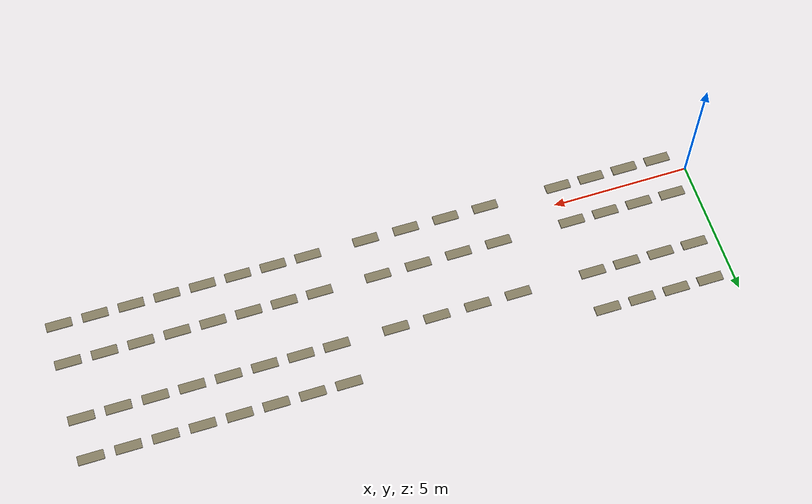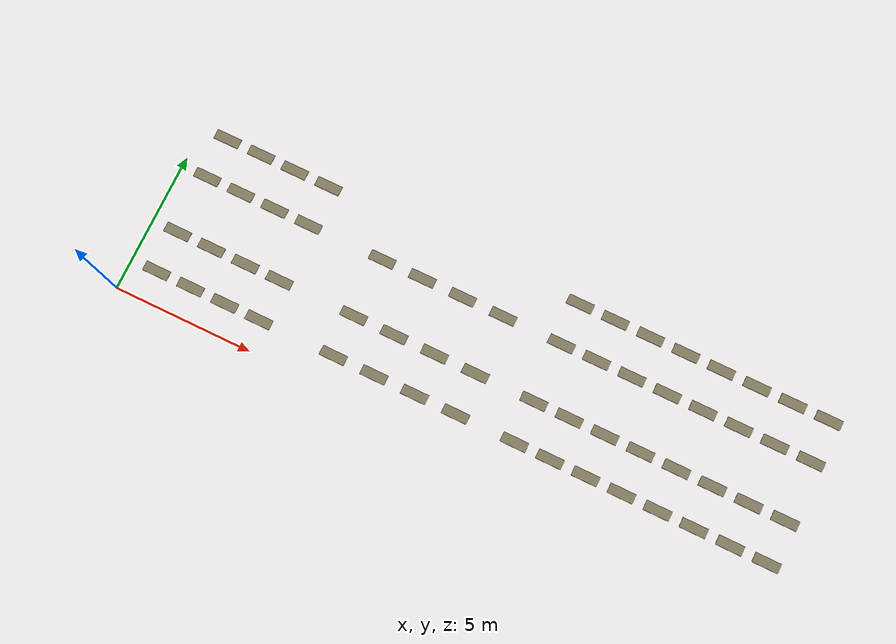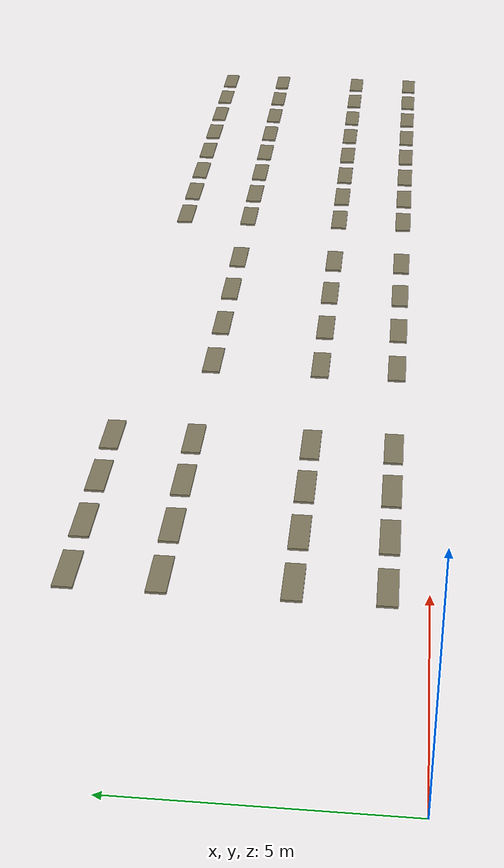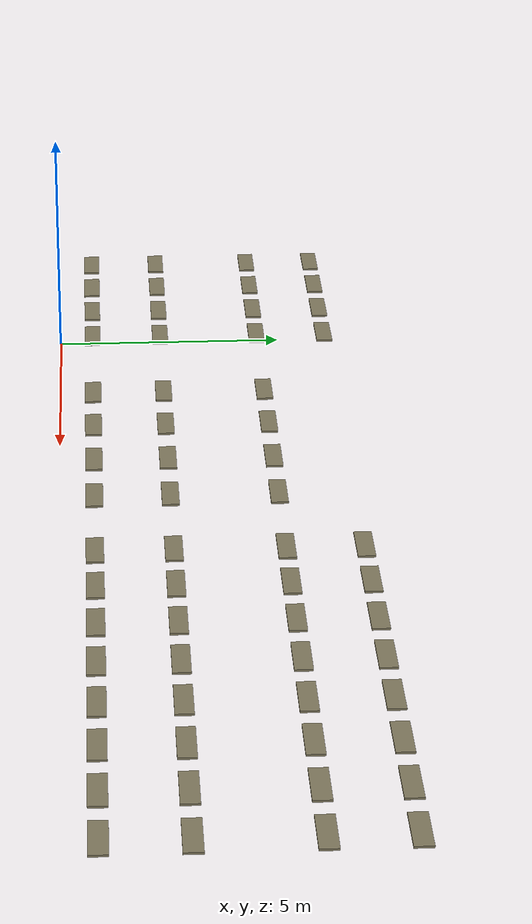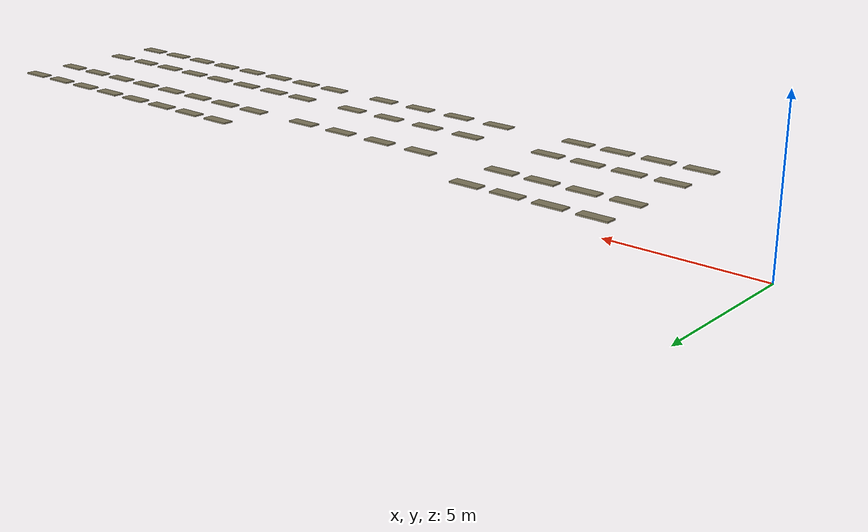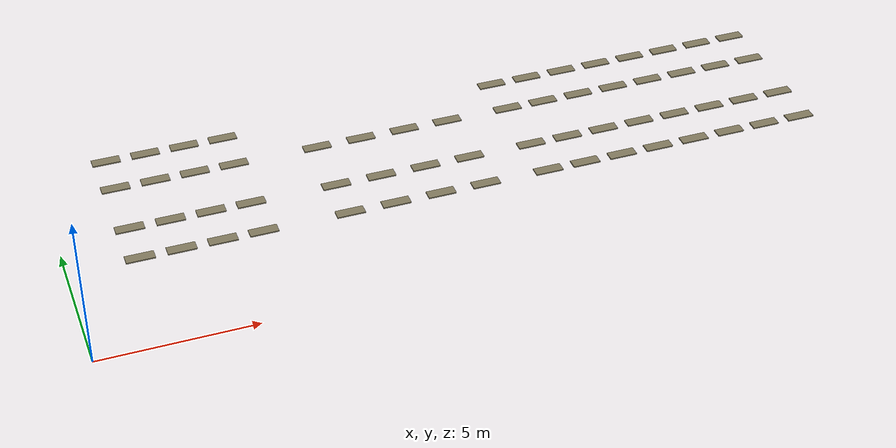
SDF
<?xml version="1.0" ?>
<sdf version="1.10">
  <model name="room_fluorescent_lights">
    <static>true</static>
    <!-- Generated from original ceiling_lights_zone* visual fixture poses. -->
    <link name="ceiling_lights_zone1_r1_c1">
      <pose>1.8 0.75 2.8 0 0 0</pose>
      <collision name="ceiling_lights_zone1_r1_c1_collision">
        <geometry>
          <box><size>0.85 0.32 0.04</size></box>
        </geometry>
      </collision>
      <visual name="ceiling_lights_zone1_r1_c1_visual">
        <pose>0 0 -0.02 0 0 0</pose>
        <geometry>
          <box><size>0.85 0.32 0.04</size></box>
        </geometry>
        <material>
          <ambient>0.38 0.36 0.29 1</ambient>
          <diffuse>0.52 0.49 0.38 1</diffuse>
          <emissive>0.30 0.27 0.19 1</emissive>
          <specular>0.06 0.06 0.05 1</specular>
        </material>
      </visual>
      <light name="ceiling_lights_zone1_r1_c1_spot" type="spot">
        <pose>0 0 -0.035 0 0 0</pose>
        <diffuse>0.32 0.305 0.265 1</diffuse>
        <specular>0.08 0.08 0.065 1</specular>
        <attenuation>
          <range>9.2</range>
          <constant>1.05</constant>
          <linear>0.23</linear>
          <quadratic>0.035</quadratic>
        </attenuation>
        <direction>0 0 -1</direction>
        <spot>
          <inner_angle>1.45</inner_angle>
          <outer_angle>2.45</outer_angle>
          <falloff>0.5</falloff>
        </spot>
        <cast_shadows>false</cast_shadows>
      </light>
    </link>
    <link name="ceiling_lights_zone1_r1_c2">
      <pose>1.8 2.15 2.8 0 0 0</pose>
      <collision name="ceiling_lights_zone1_r1_c2_collision">
        <geometry>
          <box><size>0.85 0.32 0.04</size></box>
        </geometry>
      </collision>
      <visual name="ceiling_lights_zone1_r1_c2_visual">
        <pose>0 0 -0.02 0 0 0</pose>
        <geometry>
          <box><size>0.85 0.32 0.04</size></box>
        </geometry>
        <material>
          <ambient>0.38 0.36 0.29 1</ambient>
          <diffuse>0.52 0.49 0.38 1</diffuse>
          <emissive>0.30 0.27 0.19 1</emissive>
          <specular>0.06 0.06 0.05 1</specular>
        </material>
      </visual>
      <light name="ceiling_lights_zone1_r1_c2_spot" type="spot">
        <pose>0 0 -0.035 0 0 0</pose>
        <diffuse>0.32 0.305 0.265 1</diffuse>
        <specular>0.08 0.08 0.065 1</specular>
        <attenuation>
          <range>9.2</range>
          <constant>1.05</constant>
          <linear>0.23</linear>
          <quadratic>0.035</quadratic>
        </attenuation>
        <direction>0 0 -1</direction>
        <spot>
          <inner_angle>1.45</inner_angle>
          <outer_angle>2.45</outer_angle>
          <falloff>0.5</falloff>
        </spot>
        <cast_shadows>false</cast_shadows>
      </light>
    </link>
    <link name="ceiling_lights_zone1_r1_c3">
      <pose>1.8 4.15 2.8 0 0 0</pose>
      <collision name="ceiling_lights_zone1_r1_c3_collision">
        <geometry>
          <box><size>0.85 0.32 0.04</size></box>
        </geometry>
      </collision>
      <visual name="ceiling_lights_zone1_r1_c3_visual">
        <pose>0 0 -0.02 0 0 0</pose>
        <geometry>
          <box><size>0.85 0.32 0.04</size></box>
        </geometry>
        <material>
          <ambient>0.38 0.36 0.29 1</ambient>
          <diffuse>0.52 0.49 0.38 1</diffuse>
          <emissive>0.30 0.27 0.19 1</emissive>
          <specular>0.06 0.06 0.05 1</specular>
        </material>
      </visual>
      <light name="ceiling_lights_zone1_r1_c3_spot" type="spot">
        <pose>0 0 -0.035 0 0 0</pose>
        <diffuse>0.32 0.305 0.265 1</diffuse>
        <specular>0.08 0.08 0.065 1</specular>
        <attenuation>
          <range>9.2</range>
          <constant>1.05</constant>
          <linear>0.23</linear>
          <quadratic>0.035</quadratic>
        </attenuation>
        <direction>0 0 -1</direction>
        <spot>
          <inner_angle>1.45</inner_angle>
          <outer_angle>2.45</outer_angle>
          <falloff>0.5</falloff>
        </spot>
        <cast_shadows>false</cast_shadows>
      </light>
    </link>
    <link name="ceiling_lights_zone1_r1_c4">
      <pose>1.8 5.55 2.8 0 0 0</pose>
      <collision name="ceiling_lights_zone1_r1_c4_collision">
        <geometry>
          <box><size>0.85 0.32 0.04</size></box>
        </geometry>
      </collision>
      <visual name="ceiling_lights_zone1_r1_c4_visual">
        <pose>0 0 -0.02 0 0 0</pose>
        <geometry>
          <box><size>0.85 0.32 0.04</size></box>
        </geometry>
        <material>
          <ambient>0.38 0.36 0.29 1</ambient>
          <diffuse>0.52 0.49 0.38 1</diffuse>
          <emissive>0.30 0.27 0.19 1</emissive>
          <specular>0.06 0.06 0.05 1</specular>
        </material>
      </visual>
      <light name="ceiling_lights_zone1_r1_c4_spot" type="spot">
        <pose>0 0 -0.035 0 0 0</pose>
        <diffuse>0.32 0.305 0.265 1</diffuse>
        <specular>0.08 0.08 0.065 1</specular>
        <attenuation>
          <range>9.2</range>
          <constant>1.05</constant>
          <linear>0.23</linear>
          <quadratic>0.035</quadratic>
        </attenuation>
        <direction>0 0 -1</direction>
        <spot>
          <inner_angle>1.45</inner_angle>
          <outer_angle>2.45</outer_angle>
          <falloff>0.5</falloff>
        </spot>
        <cast_shadows>false</cast_shadows>
      </light>
    </link>
    <link name="ceiling_lights_zone1_r2_c1">
      <pose>3 0.75 2.8 0 0 0</pose>
      <collision name="ceiling_lights_zone1_r2_c1_collision">
        <geometry>
          <box><size>0.85 0.32 0.04</size></box>
        </geometry>
      </collision>
      <visual name="ceiling_lights_zone1_r2_c1_visual">
        <pose>0 0 -0.02 0 0 0</pose>
        <geometry>
          <box><size>0.85 0.32 0.04</size></box>
        </geometry>
        <material>
          <ambient>0.38 0.36 0.29 1</ambient>
          <diffuse>0.52 0.49 0.38 1</diffuse>
          <emissive>0.30 0.27 0.19 1</emissive>
          <specular>0.06 0.06 0.05 1</specular>
        </material>
      </visual>
      <light name="ceiling_lights_zone1_r2_c1_spot" type="spot">
        <pose>0 0 -0.035 0 0 0</pose>
        <diffuse>0.32 0.305 0.265 1</diffuse>
        <specular>0.08 0.08 0.065 1</specular>
        <attenuation>
          <range>9.2</range>
          <constant>1.05</constant>
          <linear>0.23</linear>
          <quadratic>0.035</quadratic>
        </attenuation>
        <direction>0 0 -1</direction>
        <spot>
          <inner_angle>1.45</inner_angle>
          <outer_angle>2.45</outer_angle>
          <falloff>0.5</falloff>
        </spot>
        <cast_shadows>false</cast_shadows>
      </light>
    </link>
    <link name="ceiling_lights_zone1_r2_c2">
      <pose>3 2.15 2.8 0 0 0</pose>
      <collision name="ceiling_lights_zone1_r2_c2_collision">
        <geometry>
          <box><size>0.85 0.32 0.04</size></box>
        </geometry>
      </collision>
      <visual name="ceiling_lights_zone1_r2_c2_visual">
        <pose>0 0 -0.02 0 0 0</pose>
        <geometry>
          <box><size>0.85 0.32 0.04</size></box>
        </geometry>
        <material>
          <ambient>0.38 0.36 0.29 1</ambient>
          <diffuse>0.52 0.49 0.38 1</diffuse>
          <emissive>0.30 0.27 0.19 1</emissive>
          <specular>0.06 0.06 0.05 1</specular>
        </material>
      </visual>
      <light name="ceiling_lights_zone1_r2_c2_spot" type="spot">
        <pose>0 0 -0.035 0 0 0</pose>
        <diffuse>0.32 0.305 0.265 1</diffuse>
        <specular>0.08 0.08 0.065 1</specular>
        <attenuation>
          <range>9.2</range>
          <constant>1.05</constant>
          <linear>0.23</linear>
          <quadratic>0.035</quadratic>
        </attenuation>
        <direction>0 0 -1</direction>
        <spot>
          <inner_angle>1.45</inner_angle>
          <outer_angle>2.45</outer_angle>
          <falloff>0.5</falloff>
        </spot>
        <cast_shadows>false</cast_shadows>
      </light>
    </link>
    <link name="ceiling_lights_zone1_r2_c3">
      <pose>3 4.15 2.8 0 0 0</pose>
      <collision name="ceiling_lights_zone1_r2_c3_collision">
        <geometry>
          <box><size>0.85 0.32 0.04</size></box>
        </geometry>
      </collision>
      <visual name="ceiling_lights_zone1_r2_c3_visual">
        <pose>0 0 -0.02 0 0 0</pose>
        <geometry>
          <box><size>0.85 0.32 0.04</size></box>
        </geometry>
        <material>
          <ambient>0.38 0.36 0.29 1</ambient>
          <diffuse>0.52 0.49 0.38 1</diffuse>
          <emissive>0.30 0.27 0.19 1</emissive>
          <specular>0.06 0.06 0.05 1</specular>
        </material>
      </visual>
      <light name="ceiling_lights_zone1_r2_c3_spot" type="spot">
        <pose>0 0 -0.035 0 0 0</pose>
        <diffuse>0.32 0.305 0.265 1</diffuse>
        <specular>0.08 0.08 0.065 1</specular>
        <attenuation>
          <range>9.2</range>
          <constant>1.05</constant>
          <linear>0.23</linear>
          <quadratic>0.035</quadratic>
        </attenuation>
        <direction>0 0 -1</direction>
        <spot>
          <inner_angle>1.45</inner_angle>
          <outer_angle>2.45</outer_angle>
          <falloff>0.5</falloff>
        </spot>
        <cast_shadows>false</cast_shadows>
      </light>
    </link>
    <link name="ceiling_lights_zone1_r2_c4">
      <pose>3 5.55 2.8 0 0 0</pose>
      <collision name="ceiling_lights_zone1_r2_c4_collision">
        <geometry>
          <box><size>0.85 0.32 0.04</size></box>
        </geometry>
      </collision>
      <visual name="ceiling_lights_zone1_r2_c4_visual">
        <pose>0 0 -0.02 0 0 0</pose>
        <geometry>
          <box><size>0.85 0.32 0.04</size></box>
        </geometry>
        <material>
          <ambient>0.38 0.36 0.29 1</ambient>
          <diffuse>0.52 0.49 0.38 1</diffuse>
          <emissive>0.30 0.27 0.19 1</emissive>
          <specular>0.06 0.06 0.05 1</specular>
        </material>
      </visual>
      <light name="ceiling_lights_zone1_r2_c4_spot" type="spot">
        <pose>0 0 -0.035 0 0 0</pose>
        <diffuse>0.32 0.305 0.265 1</diffuse>
        <specular>0.08 0.08 0.065 1</specular>
        <attenuation>
          <range>9.2</range>
          <constant>1.05</constant>
          <linear>0.23</linear>
          <quadratic>0.035</quadratic>
        </attenuation>
        <direction>0 0 -1</direction>
        <spot>
          <inner_angle>1.45</inner_angle>
          <outer_angle>2.45</outer_angle>
          <falloff>0.5</falloff>
        </spot>
        <cast_shadows>false</cast_shadows>
      </light>
    </link>
    <link name="ceiling_lights_zone1_r3_c1">
      <pose>4.2 0.75 2.8 0 0 0</pose>
      <collision name="ceiling_lights_zone1_r3_c1_collision">
        <geometry>
          <box><size>0.85 0.32 0.04</size></box>
        </geometry>
      </collision>
      <visual name="ceiling_lights_zone1_r3_c1_visual">
        <pose>0 0 -0.02 0 0 0</pose>
        <geometry>
          <box><size>0.85 0.32 0.04</size></box>
        </geometry>
        <material>
          <ambient>0.38 0.36 0.29 1</ambient>
          <diffuse>0.52 0.49 0.38 1</diffuse>
          <emissive>0.30 0.27 0.19 1</emissive>
          <specular>0.06 0.06 0.05 1</specular>
        </material>
      </visual>
      <light name="ceiling_lights_zone1_r3_c1_spot" type="spot">
        <pose>0 0 -0.035 0 0 0</pose>
        <diffuse>0.32 0.305 0.265 1</diffuse>
        <specular>0.08 0.08 0.065 1</specular>
        <attenuation>
          <range>9.2</range>
          <constant>1.05</constant>
          <linear>0.23</linear>
          <quadratic>0.035</quadratic>
        </attenuation>
        <direction>0 0 -1</direction>
        <spot>
          <inner_angle>1.45</inner_angle>
          <outer_angle>2.45</outer_angle>
          <falloff>0.5</falloff>
        </spot>
        <cast_shadows>false</cast_shadows>
      </light>
    </link>
    <link name="ceiling_lights_zone1_r3_c2">
      <pose>4.2 2.15 2.8 0 0 0</pose>
      <collision name="ceiling_lights_zone1_r3_c2_collision">
        <geometry>
          <box><size>0.85 0.32 0.04</size></box>
        </geometry>
      </collision>
      <visual name="ceiling_lights_zone1_r3_c2_visual">
        <pose>0 0 -0.02 0 0 0</pose>
        <geometry>
          <box><size>0.85 0.32 0.04</size></box>
        </geometry>
        <material>
          <ambient>0.38 0.36 0.29 1</ambient>
          <diffuse>0.52 0.49 0.38 1</diffuse>
          <emissive>0.30 0.27 0.19 1</emissive>
          <specular>0.06 0.06 0.05 1</specular>
        </material>
      </visual>
      <light name="ceiling_lights_zone1_r3_c2_spot" type="spot">
        <pose>0 0 -0.035 0 0 0</pose>
        <diffuse>0.32 0.305 0.265 1</diffuse>
        <specular>0.08 0.08 0.065 1</specular>
        <attenuation>
          <range>9.2</range>
          <constant>1.05</constant>
          <linear>0.23</linear>
          <quadratic>0.035</quadratic>
        </attenuation>
        <direction>0 0 -1</direction>
        <spot>
          <inner_angle>1.45</inner_angle>
          <outer_angle>2.45</outer_angle>
          <falloff>0.5</falloff>
        </spot>
        <cast_shadows>false</cast_shadows>
      </light>
    </link>
    <link name="ceiling_lights_zone1_r3_c3">
      <pose>4.2 4.15 2.8 0 0 0</pose>
      <collision name="ceiling_lights_zone1_r3_c3_collision">
        <geometry>
          <box><size>0.85 0.32 0.04</size></box>
        </geometry>
      </collision>
      <visual name="ceiling_lights_zone1_r3_c3_visual">
        <pose>0 0 -0.02 0 0 0</pose>
        <geometry>
          <box><size>0.85 0.32 0.04</size></box>
        </geometry>
        <material>
          <ambient>0.38 0.36 0.29 1</ambient>
          <diffuse>0.52 0.49 0.38 1</diffuse>
          <emissive>0.30 0.27 0.19 1</emissive>
          <specular>0.06 0.06 0.05 1</specular>
        </material>
      </visual>
      <light name="ceiling_lights_zone1_r3_c3_spot" type="spot">
        <pose>0 0 -0.035 0 0 0</pose>
        <diffuse>0.32 0.305 0.265 1</diffuse>
        <specular>0.08 0.08 0.065 1</specular>
        <attenuation>
          <range>9.2</range>
          <constant>1.05</constant>
          <linear>0.23</linear>
          <quadratic>0.035</quadratic>
        </attenuation>
        <direction>0 0 -1</direction>
        <spot>
          <inner_angle>1.45</inner_angle>
          <outer_angle>2.45</outer_angle>
          <falloff>0.5</falloff>
        </spot>
        <cast_shadows>false</cast_shadows>
      </light>
    </link>
    <link name="ceiling_lights_zone1_r3_c4">
      <pose>4.2 5.55 2.8 0 0 0</pose>
      <collision name="ceiling_lights_zone1_r3_c4_collision">
        <geometry>
          <box><size>0.85 0.32 0.04</size></box>
        </geometry>
      </collision>
      <visual name="ceiling_lights_zone1_r3_c4_visual">
        <pose>0 0 -0.02 0 0 0</pose>
        <geometry>
          <box><size>0.85 0.32 0.04</size></box>
        </geometry>
        <material>
          <ambient>0.38 0.36 0.29 1</ambient>
          <diffuse>0.52 0.49 0.38 1</diffuse>
          <emissive>0.30 0.27 0.19 1</emissive>
          <specular>0.06 0.06 0.05 1</specular>
        </material>
      </visual>
      <light name="ceiling_lights_zone1_r3_c4_spot" type="spot">
        <pose>0 0 -0.035 0 0 0</pose>
        <diffuse>0.32 0.305 0.265 1</diffuse>
        <specular>0.08 0.08 0.065 1</specular>
        <attenuation>
          <range>9.2</range>
          <constant>1.05</constant>
          <linear>0.23</linear>
          <quadratic>0.035</quadratic>
        </attenuation>
        <direction>0 0 -1</direction>
        <spot>
          <inner_angle>1.45</inner_angle>
          <outer_angle>2.45</outer_angle>
          <falloff>0.5</falloff>
        </spot>
        <cast_shadows>false</cast_shadows>
      </light>
    </link>
    <link name="ceiling_lights_zone1_r4_c1">
      <pose>5.4 0.75 2.8 0 0 0</pose>
      <collision name="ceiling_lights_zone1_r4_c1_collision">
        <geometry>
          <box><size>0.85 0.32 0.04</size></box>
        </geometry>
      </collision>
      <visual name="ceiling_lights_zone1_r4_c1_visual">
        <pose>0 0 -0.02 0 0 0</pose>
        <geometry>
          <box><size>0.85 0.32 0.04</size></box>
        </geometry>
        <material>
          <ambient>0.38 0.36 0.29 1</ambient>
          <diffuse>0.52 0.49 0.38 1</diffuse>
          <emissive>0.30 0.27 0.19 1</emissive>
          <specular>0.06 0.06 0.05 1</specular>
        </material>
      </visual>
      <light name="ceiling_lights_zone1_r4_c1_spot" type="spot">
        <pose>0 0 -0.035 0 0 0</pose>
        <diffuse>0.32 0.305 0.265 1</diffuse>
        <specular>0.08 0.08 0.065 1</specular>
        <attenuation>
          <range>9.2</range>
          <constant>1.05</constant>
          <linear>0.23</linear>
          <quadratic>0.035</quadratic>
        </attenuation>
        <direction>0 0 -1</direction>
        <spot>
          <inner_angle>1.45</inner_angle>
          <outer_angle>2.45</outer_angle>
          <falloff>0.5</falloff>
        </spot>
        <cast_shadows>false</cast_shadows>
      </light>
    </link>
    <link name="ceiling_lights_zone1_r4_c2">
      <pose>5.4 2.15 2.8 0 0 0</pose>
      <collision name="ceiling_lights_zone1_r4_c2_collision">
        <geometry>
          <box><size>0.85 0.32 0.04</size></box>
        </geometry>
      </collision>
      <visual name="ceiling_lights_zone1_r4_c2_visual">
        <pose>0 0 -0.02 0 0 0</pose>
        <geometry>
          <box><size>0.85 0.32 0.04</size></box>
        </geometry>
        <material>
          <ambient>0.38 0.36 0.29 1</ambient>
          <diffuse>0.52 0.49 0.38 1</diffuse>
          <emissive>0.30 0.27 0.19 1</emissive>
          <specular>0.06 0.06 0.05 1</specular>
        </material>
      </visual>
      <light name="ceiling_lights_zone1_r4_c2_spot" type="spot">
        <pose>0 0 -0.035 0 0 0</pose>
        <diffuse>0.32 0.305 0.265 1</diffuse>
        <specular>0.08 0.08 0.065 1</specular>
        <attenuation>
          <range>9.2</range>
          <constant>1.05</constant>
          <linear>0.23</linear>
          <quadratic>0.035</quadratic>
        </attenuation>
        <direction>0 0 -1</direction>
        <spot>
          <inner_angle>1.45</inner_angle>
          <outer_angle>2.45</outer_angle>
          <falloff>0.5</falloff>
        </spot>
        <cast_shadows>false</cast_shadows>
      </light>
    </link>
    <link name="ceiling_lights_zone1_r4_c3">
      <pose>5.4 4.15 2.8 0 0 0</pose>
      <collision name="ceiling_lights_zone1_r4_c3_collision">
        <geometry>
          <box><size>0.85 0.32 0.04</size></box>
        </geometry>
      </collision>
      <visual name="ceiling_lights_zone1_r4_c3_visual">
        <pose>0 0 -0.02 0 0 0</pose>
        <geometry>
          <box><size>0.85 0.32 0.04</size></box>
        </geometry>
        <material>
          <ambient>0.38 0.36 0.29 1</ambient>
          <diffuse>0.52 0.49 0.38 1</diffuse>
          <emissive>0.30 0.27 0.19 1</emissive>
          <specular>0.06 0.06 0.05 1</specular>
        </material>
      </visual>
      <light name="ceiling_lights_zone1_r4_c3_spot" type="spot">
        <pose>0 0 -0.035 0 0 0</pose>
        <diffuse>0.32 0.305 0.265 1</diffuse>
        <specular>0.08 0.08 0.065 1</specular>
        <attenuation>
          <range>9.2</range>
          <constant>1.05</constant>
          <linear>0.23</linear>
          <quadratic>0.035</quadratic>
        </attenuation>
        <direction>0 0 -1</direction>
        <spot>
          <inner_angle>1.45</inner_angle>
          <outer_angle>2.45</outer_angle>
          <falloff>0.5</falloff>
        </spot>
        <cast_shadows>false</cast_shadows>
      </light>
    </link>
    <link name="ceiling_lights_zone1_r4_c4">
      <pose>5.4 5.55 2.8 0 0 0</pose>
      <collision name="ceiling_lights_zone1_r4_c4_collision">
        <geometry>
          <box><size>0.85 0.32 0.04</size></box>
        </geometry>
      </collision>
      <visual name="ceiling_lights_zone1_r4_c4_visual">
        <pose>0 0 -0.02 0 0 0</pose>
        <geometry>
          <box><size>0.85 0.32 0.04</size></box>
        </geometry>
        <material>
          <ambient>0.38 0.36 0.29 1</ambient>
          <diffuse>0.52 0.49 0.38 1</diffuse>
          <emissive>0.30 0.27 0.19 1</emissive>
          <specular>0.06 0.06 0.05 1</specular>
        </material>
      </visual>
      <light name="ceiling_lights_zone1_r4_c4_spot" type="spot">
        <pose>0 0 -0.035 0 0 0</pose>
        <diffuse>0.32 0.305 0.265 1</diffuse>
        <specular>0.08 0.08 0.065 1</specular>
        <attenuation>
          <range>9.2</range>
          <constant>1.05</constant>
          <linear>0.23</linear>
          <quadratic>0.035</quadratic>
        </attenuation>
        <direction>0 0 -1</direction>
        <spot>
          <inner_angle>1.45</inner_angle>
          <outer_angle>2.45</outer_angle>
          <falloff>0.5</falloff>
        </spot>
        <cast_shadows>false</cast_shadows>
      </light>
    </link>
    <link name="ceiling_lights_zone2_r1_c1">
      <pose>8 0.75 2.8 0 0 0</pose>
      <collision name="ceiling_lights_zone2_r1_c1_collision">
        <geometry>
          <box><size>0.85 0.32 0.04</size></box>
        </geometry>
      </collision>
      <visual name="ceiling_lights_zone2_r1_c1_visual">
        <pose>0 0 -0.02 0 0 0</pose>
        <geometry>
          <box><size>0.85 0.32 0.04</size></box>
        </geometry>
        <material>
          <ambient>0.38 0.36 0.29 1</ambient>
          <diffuse>0.52 0.49 0.38 1</diffuse>
          <emissive>0.30 0.27 0.19 1</emissive>
          <specular>0.06 0.06 0.05 1</specular>
        </material>
      </visual>
      <light name="ceiling_lights_zone2_r1_c1_spot" type="spot">
        <pose>0 0 -0.035 0 0 0</pose>
        <diffuse>0.32 0.305 0.265 1</diffuse>
        <specular>0.08 0.08 0.065 1</specular>
        <attenuation>
          <range>9.2</range>
          <constant>1.05</constant>
          <linear>0.23</linear>
          <quadratic>0.035</quadratic>
        </attenuation>
        <direction>0 0 -1</direction>
        <spot>
          <inner_angle>1.45</inner_angle>
          <outer_angle>2.45</outer_angle>
          <falloff>0.5</falloff>
        </spot>
        <cast_shadows>false</cast_shadows>
      </light>
    </link>
    <link name="ceiling_lights_zone2_r1_c2">
      <pose>8 2.15 2.8 0 0 0</pose>
      <collision name="ceiling_lights_zone2_r1_c2_collision">
        <geometry>
          <box><size>0.85 0.32 0.04</size></box>
        </geometry>
      </collision>
      <visual name="ceiling_lights_zone2_r1_c2_visual">
        <pose>0 0 -0.02 0 0 0</pose>
        <geometry>
          <box><size>0.85 0.32 0.04</size></box>
        </geometry>
        <material>
          <ambient>0.38 0.36 0.29 1</ambient>
          <diffuse>0.52 0.49 0.38 1</diffuse>
          <emissive>0.30 0.27 0.19 1</emissive>
          <specular>0.06 0.06 0.05 1</specular>
        </material>
      </visual>
      <light name="ceiling_lights_zone2_r1_c2_spot" type="spot">
        <pose>0 0 -0.035 0 0 0</pose>
        <diffuse>0.32 0.305 0.265 1</diffuse>
        <specular>0.08 0.08 0.065 1</specular>
        <attenuation>
          <range>9.2</range>
          <constant>1.05</constant>
          <linear>0.23</linear>
          <quadratic>0.035</quadratic>
        </attenuation>
        <direction>0 0 -1</direction>
        <spot>
          <inner_angle>1.45</inner_angle>
          <outer_angle>2.45</outer_angle>
          <falloff>0.5</falloff>
        </spot>
        <cast_shadows>false</cast_shadows>
      </light>
    </link>
    <link name="ceiling_lights_zone2_r1_c3">
      <pose>8 4.15 2.8 0 0 0</pose>
      <collision name="ceiling_lights_zone2_r1_c3_collision">
        <geometry>
          <box><size>0.85 0.32 0.04</size></box>
        </geometry>
      </collision>
      <visual name="ceiling_lights_zone2_r1_c3_visual">
        <pose>0 0 -0.02 0 0 0</pose>
        <geometry>
          <box><size>0.85 0.32 0.04</size></box>
        </geometry>
        <material>
          <ambient>0.38 0.36 0.29 1</ambient>
          <diffuse>0.52 0.49 0.38 1</diffuse>
          <emissive>0.30 0.27 0.19 1</emissive>
          <specular>0.06 0.06 0.05 1</specular>
        </material>
      </visual>
      <light name="ceiling_lights_zone2_r1_c3_spot" type="spot">
        <pose>0 0 -0.035 0 0 0</pose>
        <diffuse>0.32 0.305 0.265 1</diffuse>
        <specular>0.08 0.08 0.065 1</specular>
        <attenuation>
          <range>9.2</range>
          <constant>1.05</constant>
          <linear>0.23</linear>
          <quadratic>0.035</quadratic>
        </attenuation>
        <direction>0 0 -1</direction>
        <spot>
          <inner_angle>1.45</inner_angle>
          <outer_angle>2.45</outer_angle>
          <falloff>0.5</falloff>
        </spot>
        <cast_shadows>false</cast_shadows>
      </light>
    </link>
    <link name="ceiling_lights_zone2_r2_c1">
      <pose>9.4 0.75 2.8 0 0 0</pose>
      <collision name="ceiling_lights_zone2_r2_c1_collision">
        <geometry>
          <box><size>0.85 0.32 0.04</size></box>
        </geometry>
      </collision>
      <visual name="ceiling_lights_zone2_r2_c1_visual">
        <pose>0 0 -0.02 0 0 0</pose>
        <geometry>
          <box><size>0.85 0.32 0.04</size></box>
        </geometry>
        <material>
          <ambient>0.38 0.36 0.29 1</ambient>
          <diffuse>0.52 0.49 0.38 1</diffuse>
          <emissive>0.30 0.27 0.19 1</emissive>
          <specular>0.06 0.06 0.05 1</specular>
        </material>
      </visual>
      <light name="ceiling_lights_zone2_r2_c1_spot" type="spot">
        <pose>0 0 -0.035 0 0 0</pose>
        <diffuse>0.32 0.305 0.265 1</diffuse>
        <specular>0.08 0.08 0.065 1</specular>
        <attenuation>
          <range>9.2</range>
          <constant>1.05</constant>
          <linear>0.23</linear>
          <quadratic>0.035</quadratic>
        </attenuation>
        <direction>0 0 -1</direction>
        <spot>
          <inner_angle>1.45</inner_angle>
          <outer_angle>2.45</outer_angle>
          <falloff>0.5</falloff>
        </spot>
        <cast_shadows>false</cast_shadows>
      </light>
    </link>
    <link name="ceiling_lights_zone2_r2_c2">
      <pose>9.4 2.15 2.8 0 0 0</pose>
      <collision name="ceiling_lights_zone2_r2_c2_collision">
        <geometry>
          <box><size>0.85 0.32 0.04</size></box>
        </geometry>
      </collision>
      <visual name="ceiling_lights_zone2_r2_c2_visual">
        <pose>0 0 -0.02 0 0 0</pose>
        <geometry>
          <box><size>0.85 0.32 0.04</size></box>
        </geometry>
        <material>
          <ambient>0.38 0.36 0.29 1</ambient>
          <diffuse>0.52 0.49 0.38 1</diffuse>
          <emissive>0.30 0.27 0.19 1</emissive>
          <specular>0.06 0.06 0.05 1</specular>
        </material>
      </visual>
      <light name="ceiling_lights_zone2_r2_c2_spot" type="spot">
        <pose>0 0 -0.035 0 0 0</pose>
        <diffuse>0.32 0.305 0.265 1</diffuse>
        <specular>0.08 0.08 0.065 1</specular>
        <attenuation>
          <range>9.2</range>
          <constant>1.05</constant>
          <linear>0.23</linear>
          <quadratic>0.035</quadratic>
        </attenuation>
        <direction>0 0 -1</direction>
        <spot>
          <inner_angle>1.45</inner_angle>
          <outer_angle>2.45</outer_angle>
          <falloff>0.5</falloff>
        </spot>
        <cast_shadows>false</cast_shadows>
      </light>
    </link>
    <link name="ceiling_lights_zone2_r2_c3">
      <pose>9.4 4.15 2.8 0 0 0</pose>
      <collision name="ceiling_lights_zone2_r2_c3_collision">
        <geometry>
          <box><size>0.85 0.32 0.04</size></box>
        </geometry>
      </collision>
      <visual name="ceiling_lights_zone2_r2_c3_visual">
        <pose>0 0 -0.02 0 0 0</pose>
        <geometry>
          <box><size>0.85 0.32 0.04</size></box>
        </geometry>
        <material>
          <ambient>0.38 0.36 0.29 1</ambient>
          <diffuse>0.52 0.49 0.38 1</diffuse>
          <emissive>0.30 0.27 0.19 1</emissive>
          <specular>0.06 0.06 0.05 1</specular>
        </material>
      </visual>
      <light name="ceiling_lights_zone2_r2_c3_spot" type="spot">
        <pose>0 0 -0.035 0 0 0</pose>
        <diffuse>0.32 0.305 0.265 1</diffuse>
        <specular>0.08 0.08 0.065 1</specular>
        <attenuation>
          <range>9.2</range>
          <constant>1.05</constant>
          <linear>0.23</linear>
          <quadratic>0.035</quadratic>
        </attenuation>
        <direction>0 0 -1</direction>
        <spot>
          <inner_angle>1.45</inner_angle>
          <outer_angle>2.45</outer_angle>
          <falloff>0.5</falloff>
        </spot>
        <cast_shadows>false</cast_shadows>
      </light>
    </link>
    <link name="ceiling_lights_zone2_r3_c1">
      <pose>10.8 0.75 2.8 0 0 0</pose>
      <collision name="ceiling_lights_zone2_r3_c1_collision">
        <geometry>
          <box><size>0.85 0.32 0.04</size></box>
        </geometry>
      </collision>
      <visual name="ceiling_lights_zone2_r3_c1_visual">
        <pose>0 0 -0.02 0 0 0</pose>
        <geometry>
          <box><size>0.85 0.32 0.04</size></box>
        </geometry>
        <material>
          <ambient>0.38 0.36 0.29 1</ambient>
          <diffuse>0.52 0.49 0.38 1</diffuse>
          <emissive>0.30 0.27 0.19 1</emissive>
          <specular>0.06 0.06 0.05 1</specular>
        </material>
      </visual>
      <light name="ceiling_lights_zone2_r3_c1_spot" type="spot">
        <pose>0 0 -0.035 0 0 0</pose>
        <diffuse>0.32 0.305 0.265 1</diffuse>
        <specular>0.08 0.08 0.065 1</specular>
        <attenuation>
          <range>9.2</range>
          <constant>1.05</constant>
          <linear>0.23</linear>
          <quadratic>0.035</quadratic>
        </attenuation>
        <direction>0 0 -1</direction>
        <spot>
          <inner_angle>1.45</inner_angle>
          <outer_angle>2.45</outer_angle>
          <falloff>0.5</falloff>
        </spot>
        <cast_shadows>false</cast_shadows>
      </light>
    </link>
    <link name="ceiling_lights_zone2_r3_c2">
      <pose>10.8 2.15 2.8 0 0 0</pose>
      <collision name="ceiling_lights_zone2_r3_c2_collision">
        <geometry>
          <box><size>0.85 0.32 0.04</size></box>
        </geometry>
      </collision>
      <visual name="ceiling_lights_zone2_r3_c2_visual">
        <pose>0 0 -0.02 0 0 0</pose>
        <geometry>
          <box><size>0.85 0.32 0.04</size></box>
        </geometry>
        <material>
          <ambient>0.38 0.36 0.29 1</ambient>
          <diffuse>0.52 0.49 0.38 1</diffuse>
          <emissive>0.30 0.27 0.19 1</emissive>
          <specular>0.06 0.06 0.05 1</specular>
        </material>
      </visual>
      <light name="ceiling_lights_zone2_r3_c2_spot" type="spot">
        <pose>0 0 -0.035 0 0 0</pose>
        <diffuse>0.32 0.305 0.265 1</diffuse>
        <specular>0.08 0.08 0.065 1</specular>
        <attenuation>
          <range>9.2</range>
          <constant>1.05</constant>
          <linear>0.23</linear>
          <quadratic>0.035</quadratic>
        </attenuation>
        <direction>0 0 -1</direction>
        <spot>
          <inner_angle>1.45</inner_angle>
          <outer_angle>2.45</outer_angle>
          <falloff>0.5</falloff>
        </spot>
        <cast_shadows>false</cast_shadows>
      </light>
    </link>
    <link name="ceiling_lights_zone2_r3_c3">
      <pose>10.8 4.15 2.8 0 0 0</pose>
      <collision name="ceiling_lights_zone2_r3_c3_collision">
        <geometry>
          <box><size>0.85 0.32 0.04</size></box>
        </geometry>
      </collision>
      <visual name="ceiling_lights_zone2_r3_c3_visual">
        <pose>0 0 -0.02 0 0 0</pose>
        <geometry>
          <box><size>0.85 0.32 0.04</size></box>
        </geometry>
        <material>
          <ambient>0.38 0.36 0.29 1</ambient>
          <diffuse>0.52 0.49 0.38 1</diffuse>
          <emissive>0.30 0.27 0.19 1</emissive>
          <specular>0.06 0.06 0.05 1</specular>
        </material>
      </visual>
      <light name="ceiling_lights_zone2_r3_c3_spot" type="spot">
        <pose>0 0 -0.035 0 0 0</pose>
        <diffuse>0.32 0.305 0.265 1</diffuse>
        <specular>0.08 0.08 0.065 1</specular>
        <attenuation>
          <range>9.2</range>
          <constant>1.05</constant>
          <linear>0.23</linear>
          <quadratic>0.035</quadratic>
        </attenuation>
        <direction>0 0 -1</direction>
        <spot>
          <inner_angle>1.45</inner_angle>
          <outer_angle>2.45</outer_angle>
          <falloff>0.5</falloff>
        </spot>
        <cast_shadows>false</cast_shadows>
      </light>
    </link>
    <link name="ceiling_lights_zone2_r4_c1">
      <pose>12.2 0.75 2.8 0 0 0</pose>
      <collision name="ceiling_lights_zone2_r4_c1_collision">
        <geometry>
          <box><size>0.85 0.32 0.04</size></box>
        </geometry>
      </collision>
      <visual name="ceiling_lights_zone2_r4_c1_visual">
        <pose>0 0 -0.02 0 0 0</pose>
        <geometry>
          <box><size>0.85 0.32 0.04</size></box>
        </geometry>
        <material>
          <ambient>0.38 0.36 0.29 1</ambient>
          <diffuse>0.52 0.49 0.38 1</diffuse>
          <emissive>0.30 0.27 0.19 1</emissive>
          <specular>0.06 0.06 0.05 1</specular>
        </material>
      </visual>
      <light name="ceiling_lights_zone2_r4_c1_spot" type="spot">
        <pose>0 0 -0.035 0 0 0</pose>
        <diffuse>0.32 0.305 0.265 1</diffuse>
        <specular>0.08 0.08 0.065 1</specular>
        <attenuation>
          <range>9.2</range>
          <constant>1.05</constant>
          <linear>0.23</linear>
          <quadratic>0.035</quadratic>
        </attenuation>
        <direction>0 0 -1</direction>
        <spot>
          <inner_angle>1.45</inner_angle>
          <outer_angle>2.45</outer_angle>
          <falloff>0.5</falloff>
        </spot>
        <cast_shadows>false</cast_shadows>
      </light>
    </link>
    <link name="ceiling_lights_zone2_r4_c2">
      <pose>12.2 2.15 2.8 0 0 0</pose>
      <collision name="ceiling_lights_zone2_r4_c2_collision">
        <geometry>
          <box><size>0.85 0.32 0.04</size></box>
        </geometry>
      </collision>
      <visual name="ceiling_lights_zone2_r4_c2_visual">
        <pose>0 0 -0.02 0 0 0</pose>
        <geometry>
          <box><size>0.85 0.32 0.04</size></box>
        </geometry>
        <material>
          <ambient>0.38 0.36 0.29 1</ambient>
          <diffuse>0.52 0.49 0.38 1</diffuse>
          <emissive>0.30 0.27 0.19 1</emissive>
          <specular>0.06 0.06 0.05 1</specular>
        </material>
      </visual>
      <light name="ceiling_lights_zone2_r4_c2_spot" type="spot">
        <pose>0 0 -0.035 0 0 0</pose>
        <diffuse>0.32 0.305 0.265 1</diffuse>
        <specular>0.08 0.08 0.065 1</specular>
        <attenuation>
          <range>9.2</range>
          <constant>1.05</constant>
          <linear>0.23</linear>
          <quadratic>0.035</quadratic>
        </attenuation>
        <direction>0 0 -1</direction>
        <spot>
          <inner_angle>1.45</inner_angle>
          <outer_angle>2.45</outer_angle>
          <falloff>0.5</falloff>
        </spot>
        <cast_shadows>false</cast_shadows>
      </light>
    </link>
    <link name="ceiling_lights_zone2_r4_c3">
      <pose>12.2 4.15 2.8 0 0 0</pose>
      <collision name="ceiling_lights_zone2_r4_c3_collision">
        <geometry>
          <box><size>0.85 0.32 0.04</size></box>
        </geometry>
      </collision>
      <visual name="ceiling_lights_zone2_r4_c3_visual">
        <pose>0 0 -0.02 0 0 0</pose>
        <geometry>
          <box><size>0.85 0.32 0.04</size></box>
        </geometry>
        <material>
          <ambient>0.38 0.36 0.29 1</ambient>
          <diffuse>0.52 0.49 0.38 1</diffuse>
          <emissive>0.30 0.27 0.19 1</emissive>
          <specular>0.06 0.06 0.05 1</specular>
        </material>
      </visual>
      <light name="ceiling_lights_zone2_r4_c3_spot" type="spot">
        <pose>0 0 -0.035 0 0 0</pose>
        <diffuse>0.32 0.305 0.265 1</diffuse>
        <specular>0.08 0.08 0.065 1</specular>
        <attenuation>
          <range>9.2</range>
          <constant>1.05</constant>
          <linear>0.23</linear>
          <quadratic>0.035</quadratic>
        </attenuation>
        <direction>0 0 -1</direction>
        <spot>
          <inner_angle>1.45</inner_angle>
          <outer_angle>2.45</outer_angle>
          <falloff>0.5</falloff>
        </spot>
        <cast_shadows>false</cast_shadows>
      </light>
    </link>
    <link name="ceiling_lights_zone3_r1_c1">
      <pose>14.2 0.75 2.8 0 0 0</pose>
      <collision name="ceiling_lights_zone3_r1_c1_collision">
        <geometry>
          <box><size>0.85 0.32 0.04</size></box>
        </geometry>
      </collision>
      <visual name="ceiling_lights_zone3_r1_c1_visual">
        <pose>0 0 -0.02 0 0 0</pose>
        <geometry>
          <box><size>0.85 0.32 0.04</size></box>
        </geometry>
        <material>
          <ambient>0.38 0.36 0.29 1</ambient>
          <diffuse>0.52 0.49 0.38 1</diffuse>
          <emissive>0.30 0.27 0.19 1</emissive>
          <specular>0.06 0.06 0.05 1</specular>
        </material>
      </visual>
      <light name="ceiling_lights_zone3_r1_c1_spot" type="spot">
        <pose>0 0 -0.035 0 0 0</pose>
        <diffuse>0.32 0.305 0.265 1</diffuse>
        <specular>0.08 0.08 0.065 1</specular>
        <attenuation>
          <range>9.2</range>
          <constant>1.05</constant>
          <linear>0.23</linear>
          <quadratic>0.035</quadratic>
        </attenuation>
        <direction>0 0 -1</direction>
        <spot>
          <inner_angle>1.45</inner_angle>
          <outer_angle>2.45</outer_angle>
          <falloff>0.5</falloff>
        </spot>
        <cast_shadows>false</cast_shadows>
      </light>
    </link>
    <link name="ceiling_lights_zone3_r1_c2">
      <pose>14.2 2.15 2.8 0 0 0</pose>
      <collision name="ceiling_lights_zone3_r1_c2_collision">
        <geometry>
          <box><size>0.85 0.32 0.04</size></box>
        </geometry>
      </collision>
      <visual name="ceiling_lights_zone3_r1_c2_visual">
        <pose>0 0 -0.02 0 0 0</pose>
        <geometry>
          <box><size>0.85 0.32 0.04</size></box>
        </geometry>
        <material>
          <ambient>0.38 0.36 0.29 1</ambient>
          <diffuse>0.52 0.49 0.38 1</diffuse>
          <emissive>0.30 0.27 0.19 1</emissive>
          <specular>0.06 0.06 0.05 1</specular>
        </material>
      </visual>
      <light name="ceiling_lights_zone3_r1_c2_spot" type="spot">
        <pose>0 0 -0.035 0 0 0</pose>
        <diffuse>0.32 0.305 0.265 1</diffuse>
        <specular>0.08 0.08 0.065 1</specular>
        <attenuation>
          <range>9.2</range>
          <constant>1.05</constant>
          <linear>0.23</linear>
          <quadratic>0.035</quadratic>
        </attenuation>
        <direction>0 0 -1</direction>
        <spot>
          <inner_angle>1.45</inner_angle>
          <outer_angle>2.45</outer_angle>
          <falloff>0.5</falloff>
        </spot>
        <cast_shadows>false</cast_shadows>
      </light>
    </link>
    <link name="ceiling_lights_zone3_r1_c3">
      <pose>14.2 4.15 2.8 0 0 0</pose>
      <collision name="ceiling_lights_zone3_r1_c3_collision">
        <geometry>
          <box><size>0.85 0.32 0.04</size></box>
        </geometry>
      </collision>
      <visual name="ceiling_lights_zone3_r1_c3_visual">
        <pose>0 0 -0.02 0 0 0</pose>
        <geometry>
          <box><size>0.85 0.32 0.04</size></box>
        </geometry>
        <material>
          <ambient>0.38 0.36 0.29 1</ambient>
          <diffuse>0.52 0.49 0.38 1</diffuse>
          <emissive>0.30 0.27 0.19 1</emissive>
          <specular>0.06 0.06 0.05 1</specular>
        </material>
      </visual>
      <light name="ceiling_lights_zone3_r1_c3_spot" type="spot">
        <pose>0 0 -0.035 0 0 0</pose>
        <diffuse>0.32 0.305 0.265 1</diffuse>
        <specular>0.08 0.08 0.065 1</specular>
        <attenuation>
          <range>9.2</range>
          <constant>1.05</constant>
          <linear>0.23</linear>
          <quadratic>0.035</quadratic>
        </attenuation>
        <direction>0 0 -1</direction>
        <spot>
          <inner_angle>1.45</inner_angle>
          <outer_angle>2.45</outer_angle>
          <falloff>0.5</falloff>
        </spot>
        <cast_shadows>false</cast_shadows>
      </light>
    </link>
    <link name="ceiling_lights_zone3_r1_c4">
      <pose>14.2 5.55 2.8 0 0 0</pose>
      <collision name="ceiling_lights_zone3_r1_c4_collision">
        <geometry>
          <box><size>0.85 0.32 0.04</size></box>
        </geometry>
      </collision>
      <visual name="ceiling_lights_zone3_r1_c4_visual">
        <pose>0 0 -0.02 0 0 0</pose>
        <geometry>
          <box><size>0.85 0.32 0.04</size></box>
        </geometry>
        <material>
          <ambient>0.38 0.36 0.29 1</ambient>
          <diffuse>0.52 0.49 0.38 1</diffuse>
          <emissive>0.30 0.27 0.19 1</emissive>
          <specular>0.06 0.06 0.05 1</specular>
        </material>
      </visual>
      <light name="ceiling_lights_zone3_r1_c4_spot" type="spot">
        <pose>0 0 -0.035 0 0 0</pose>
        <diffuse>0.32 0.305 0.265 1</diffuse>
        <specular>0.08 0.08 0.065 1</specular>
        <attenuation>
          <range>9.2</range>
          <constant>1.05</constant>
          <linear>0.23</linear>
          <quadratic>0.035</quadratic>
        </attenuation>
        <direction>0 0 -1</direction>
        <spot>
          <inner_angle>1.45</inner_angle>
          <outer_angle>2.45</outer_angle>
          <falloff>0.5</falloff>
        </spot>
        <cast_shadows>false</cast_shadows>
      </light>
    </link>
    <link name="ceiling_lights_zone3_r2_c1">
      <pose>15.4 0.75 2.8 0 0 0</pose>
      <collision name="ceiling_lights_zone3_r2_c1_collision">
        <geometry>
          <box><size>0.85 0.32 0.04</size></box>
        </geometry>
      </collision>
      <visual name="ceiling_lights_zone3_r2_c1_visual">
        <pose>0 0 -0.02 0 0 0</pose>
        <geometry>
          <box><size>0.85 0.32 0.04</size></box>
        </geometry>
        <material>
          <ambient>0.38 0.36 0.29 1</ambient>
          <diffuse>0.52 0.49 0.38 1</diffuse>
          <emissive>0.30 0.27 0.19 1</emissive>
          <specular>0.06 0.06 0.05 1</specular>
        </material>
      </visual>
      <light name="ceiling_lights_zone3_r2_c1_spot" type="spot">
        <pose>0 0 -0.035 0 0 0</pose>
        <diffuse>0.32 0.305 0.265 1</diffuse>
        <specular>0.08 0.08 0.065 1</specular>
        <attenuation>
          <range>9.2</range>
          <constant>1.05</constant>
          <linear>0.23</linear>
          <quadratic>0.035</quadratic>
        </attenuation>
        <direction>0 0 -1</direction>
        <spot>
          <inner_angle>1.45</inner_angle>
          <outer_angle>2.45</outer_angle>
          <falloff>0.5</falloff>
        </spot>
        <cast_shadows>false</cast_shadows>
      </light>
    </link>
    <link name="ceiling_lights_zone3_r2_c2">
      <pose>15.4 2.15 2.8 0 0 0</pose>
      <collision name="ceiling_lights_zone3_r2_c2_collision">
        <geometry>
          <box><size>0.85 0.32 0.04</size></box>
        </geometry>
      </collision>
      <visual name="ceiling_lights_zone3_r2_c2_visual">
        <pose>0 0 -0.02 0 0 0</pose>
        <geometry>
          <box><size>0.85 0.32 0.04</size></box>
        </geometry>
        <material>
          <ambient>0.38 0.36 0.29 1</ambient>
          <diffuse>0.52 0.49 0.38 1</diffuse>
          <emissive>0.30 0.27 0.19 1</emissive>
          <specular>0.06 0.06 0.05 1</specular>
        </material>
      </visual>
      <light name="ceiling_lights_zone3_r2_c2_spot" type="spot">
        <pose>0 0 -0.035 0 0 0</pose>
        <diffuse>0.32 0.305 0.265 1</diffuse>
        <specular>0.08 0.08 0.065 1</specular>
        <attenuation>
          <range>9.2</range>
          <constant>1.05</constant>
          <linear>0.23</linear>
          <quadratic>0.035</quadratic>
        </attenuation>
        <direction>0 0 -1</direction>
        <spot>
          <inner_angle>1.45</inner_angle>
          <outer_angle>2.45</outer_angle>
          <falloff>0.5</falloff>
        </spot>
        <cast_shadows>false</cast_shadows>
      </light>
    </link>
    <link name="ceiling_lights_zone3_r2_c3">
      <pose>15.4 4.15 2.8 0 0 0</pose>
      <collision name="ceiling_lights_zone3_r2_c3_collision">
        <geometry>
          <box><size>0.85 0.32 0.04</size></box>
        </geometry>
      </collision>
      <visual name="ceiling_lights_zone3_r2_c3_visual">
        <pose>0 0 -0.02 0 0 0</pose>
        <geometry>
          <box><size>0.85 0.32 0.04</size></box>
        </geometry>
        <material>
          <ambient>0.38 0.36 0.29 1</ambient>
          <diffuse>0.52 0.49 0.38 1</diffuse>
          <emissive>0.30 0.27 0.19 1</emissive>
          <specular>0.06 0.06 0.05 1</specular>
        </material>
      </visual>
      <light name="ceiling_lights_zone3_r2_c3_spot" type="spot">
        <pose>0 0 -0.035 0 0 0</pose>
        <diffuse>0.32 0.305 0.265 1</diffuse>
        <specular>0.08 0.08 0.065 1</specular>
        <attenuation>
          <range>9.2</range>
          <constant>1.05</constant>
          <linear>0.23</linear>
          <quadratic>0.035</quadratic>
        </attenuation>
        <direction>0 0 -1</direction>
        <spot>
          <inner_angle>1.45</inner_angle>
          <outer_angle>2.45</outer_angle>
          <falloff>0.5</falloff>
        </spot>
        <cast_shadows>false</cast_shadows>
      </light>
    </link>
    <link name="ceiling_lights_zone3_r2_c4">
      <pose>15.4 5.55 2.8 0 0 0</pose>
      <collision name="ceiling_lights_zone3_r2_c4_collision">
        <geometry>
          <box><size>0.85 0.32 0.04</size></box>
        </geometry>
      </collision>
      <visual name="ceiling_lights_zone3_r2_c4_visual">
        <pose>0 0 -0.02 0 0 0</pose>
        <geometry>
          <box><size>0.85 0.32 0.04</size></box>
        </geometry>
        <material>
          <ambient>0.38 0.36 0.29 1</ambient>
          <diffuse>0.52 0.49 0.38 1</diffuse>
          <emissive>0.30 0.27 0.19 1</emissive>
          <specular>0.06 0.06 0.05 1</specular>
        </material>
      </visual>
      <light name="ceiling_lights_zone3_r2_c4_spot" type="spot">
        <pose>0 0 -0.035 0 0 0</pose>
        <diffuse>0.32 0.305 0.265 1</diffuse>
        <specular>0.08 0.08 0.065 1</specular>
        <attenuation>
          <range>9.2</range>
          <constant>1.05</constant>
          <linear>0.23</linear>
          <quadratic>0.035</quadratic>
        </attenuation>
        <direction>0 0 -1</direction>
        <spot>
          <inner_angle>1.45</inner_angle>
          <outer_angle>2.45</outer_angle>
          <falloff>0.5</falloff>
        </spot>
        <cast_shadows>false</cast_shadows>
      </light>
    </link>
    <link name="ceiling_lights_zone3_r3_c1">
      <pose>16.6 0.75 2.8 0 0 0</pose>
      <collision name="ceiling_lights_zone3_r3_c1_collision">
        <geometry>
          <box><size>0.85 0.32 0.04</size></box>
        </geometry>
      </collision>
      <visual name="ceiling_lights_zone3_r3_c1_visual">
        <pose>0 0 -0.02 0 0 0</pose>
        <geometry>
          <box><size>0.85 0.32 0.04</size></box>
        </geometry>
        <material>
          <ambient>0.38 0.36 0.29 1</ambient>
          <diffuse>0.52 0.49 0.38 1</diffuse>
          <emissive>0.30 0.27 0.19 1</emissive>
          <specular>0.06 0.06 0.05 1</specular>
        </material>
      </visual>
      <light name="ceiling_lights_zone3_r3_c1_spot" type="spot">
        <pose>0 0 -0.035 0 0 0</pose>
        <diffuse>0.32 0.305 0.265 1</diffuse>
        <specular>0.08 0.08 0.065 1</specular>
        <attenuation>
          <range>9.2</range>
          <constant>1.05</constant>
          <linear>0.23</linear>
          <quadratic>0.035</quadratic>
        </attenuation>
        <direction>0 0 -1</direction>
        <spot>
          <inner_angle>1.45</inner_angle>
          <outer_angle>2.45</outer_angle>
          <falloff>0.5</falloff>
        </spot>
        <cast_shadows>false</cast_shadows>
      </light>
    </link>
    <link name="ceiling_lights_zone3_r3_c2">
      <pose>16.6 2.15 2.8 0 0 0</pose>
      <collision name="ceiling_lights_zone3_r3_c2_collision">
        <geometry>
          <box><size>0.85 0.32 0.04</size></box>
        </geometry>
      </collision>
      <visual name="ceiling_lights_zone3_r3_c2_visual">
        <pose>0 0 -0.02 0 0 0</pose>
        <geometry>
          <box><size>0.85 0.32 0.04</size></box>
        </geometry>
        <material>
          <ambient>0.38 0.36 0.29 1</ambient>
          <diffuse>0.52 0.49 0.38 1</diffuse>
          <emissive>0.30 0.27 0.19 1</emissive>
          <specular>0.06 0.06 0.05 1</specular>
        </material>
      </visual>
      <light name="ceiling_lights_zone3_r3_c2_spot" type="spot">
        <pose>0 0 -0.035 0 0 0</pose>
        <diffuse>0.32 0.305 0.265 1</diffuse>
        <specular>0.08 0.08 0.065 1</specular>
        <attenuation>
          <range>9.2</range>
          <constant>1.05</constant>
          <linear>0.23</linear>
          <quadratic>0.035</quadratic>
        </attenuation>
        <direction>0 0 -1</direction>
        <spot>
          <inner_angle>1.45</inner_angle>
          <outer_angle>2.45</outer_angle>
          <falloff>0.5</falloff>
        </spot>
        <cast_shadows>false</cast_shadows>
      </light>
    </link>
    <link name="ceiling_lights_zone3_r3_c3">
      <pose>16.6 4.15 2.8 0 0 0</pose>
      <collision name="ceiling_lights_zone3_r3_c3_collision">
        <geometry>
          <box><size>0.85 0.32 0.04</size></box>
        </geometry>
      </collision>
      <visual name="ceiling_lights_zone3_r3_c3_visual">
        <pose>0 0 -0.02 0 0 0</pose>
        <geometry>
          <box><size>0.85 0.32 0.04</size></box>
        </geometry>
        <material>
          <ambient>0.38 0.36 0.29 1</ambient>
          <diffuse>0.52 0.49 0.38 1</diffuse>
          <emissive>0.30 0.27 0.19 1</emissive>
          <specular>0.06 0.06 0.05 1</specular>
        </material>
      </visual>
      <light name="ceiling_lights_zone3_r3_c3_spot" type="spot">
        <pose>0 0 -0.035 0 0 0</pose>
        <diffuse>0.32 0.305 0.265 1</diffuse>
        <specular>0.08 0.08 0.065 1</specular>
        <attenuation>
          <range>9.2</range>
          <constant>1.05</constant>
          <linear>0.23</linear>
          <quadratic>0.035</quadratic>
        </attenuation>
        <direction>0 0 -1</direction>
        <spot>
          <inner_angle>1.45</inner_angle>
          <outer_angle>2.45</outer_angle>
          <falloff>0.5</falloff>
        </spot>
        <cast_shadows>false</cast_shadows>
      </light>
    </link>
    <link name="ceiling_lights_zone3_r3_c4">
      <pose>16.6 5.55 2.8 0 0 0</pose>
      <collision name="ceiling_lights_zone3_r3_c4_collision">
        <geometry>
          <box><size>0.85 0.32 0.04</size></box>
        </geometry>
      </collision>
      <visual name="ceiling_lights_zone3_r3_c4_visual">
        <pose>0 0 -0.02 0 0 0</pose>
        <geometry>
          <box><size>0.85 0.32 0.04</size></box>
        </geometry>
        <material>
          <ambient>0.38 0.36 0.29 1</ambient>
          <diffuse>0.52 0.49 0.38 1</diffuse>
          <emissive>0.30 0.27 0.19 1</emissive>
          <specular>0.06 0.06 0.05 1</specular>
        </material>
      </visual>
      <light name="ceiling_lights_zone3_r3_c4_spot" type="spot">
        <pose>0 0 -0.035 0 0 0</pose>
        <diffuse>0.32 0.305 0.265 1</diffuse>
        <specular>0.08 0.08 0.065 1</specular>
        <attenuation>
          <range>9.2</range>
          <constant>1.05</constant>
          <linear>0.23</linear>
          <quadratic>0.035</quadratic>
        </attenuation>
        <direction>0 0 -1</direction>
        <spot>
          <inner_angle>1.45</inner_angle>
          <outer_angle>2.45</outer_angle>
          <falloff>0.5</falloff>
        </spot>
        <cast_shadows>false</cast_shadows>
      </light>
    </link>
    <link name="ceiling_lights_zone3_r4_c1">
      <pose>17.8 0.75 2.8 0 0 0</pose>
      <collision name="ceiling_lights_zone3_r4_c1_collision">
        <geometry>
          <box><size>0.85 0.32 0.04</size></box>
        </geometry>
      </collision>
      <visual name="ceiling_lights_zone3_r4_c1_visual">
        <pose>0 0 -0.02 0 0 0</pose>
        <geometry>
          <box><size>0.85 0.32 0.04</size></box>
        </geometry>
        <material>
          <ambient>0.38 0.36 0.29 1</ambient>
          <diffuse>0.52 0.49 0.38 1</diffuse>
          <emissive>0.30 0.27 0.19 1</emissive>
          <specular>0.06 0.06 0.05 1</specular>
        </material>
      </visual>
      <light name="ceiling_lights_zone3_r4_c1_spot" type="spot">
        <pose>0 0 -0.035 0 0 0</pose>
        <diffuse>0.32 0.305 0.265 1</diffuse>
        <specular>0.08 0.08 0.065 1</specular>
        <attenuation>
          <range>9.2</range>
          <constant>1.05</constant>
          <linear>0.23</linear>
          <quadratic>0.035</quadratic>
        </attenuation>
        <direction>0 0 -1</direction>
        <spot>
          <inner_angle>1.45</inner_angle>
          <outer_angle>2.45</outer_angle>
          <falloff>0.5</falloff>
        </spot>
        <cast_shadows>false</cast_shadows>
      </light>
    </link>
    <link name="ceiling_lights_zone3_r4_c2">
      <pose>17.8 2.15 2.8 0 0 0</pose>
      <collision name="ceiling_lights_zone3_r4_c2_collision">
        <geometry>
          <box><size>0.85 0.32 0.04</size></box>
        </geometry>
      </collision>
      <visual name="ceiling_lights_zone3_r4_c2_visual">
        <pose>0 0 -0.02 0 0 0</pose>
        <geometry>
          <box><size>0.85 0.32 0.04</size></box>
        </geometry>
        <material>
          <ambient>0.38 0.36 0.29 1</ambient>
          <diffuse>0.52 0.49 0.38 1</diffuse>
          <emissive>0.30 0.27 0.19 1</emissive>
          <specular>0.06 0.06 0.05 1</specular>
        </material>
      </visual>
      <light name="ceiling_lights_zone3_r4_c2_spot" type="spot">
        <pose>0 0 -0.035 0 0 0</pose>
        <diffuse>0.32 0.305 0.265 1</diffuse>
        <specular>0.08 0.08 0.065 1</specular>
        <attenuation>
          <range>9.2</range>
          <constant>1.05</constant>
          <linear>0.23</linear>
          <quadratic>0.035</quadratic>
        </attenuation>
        <direction>0 0 -1</direction>
        <spot>
          <inner_angle>1.45</inner_angle>
          <outer_angle>2.45</outer_angle>
          <falloff>0.5</falloff>
        </spot>
        <cast_shadows>false</cast_shadows>
      </light>
    </link>
    <link name="ceiling_lights_zone3_r4_c3">
      <pose>17.8 4.15 2.8 0 0 0</pose>
      <collision name="ceiling_lights_zone3_r4_c3_collision">
        <geometry>
          <box><size>0.85 0.32 0.04</size></box>
        </geometry>
      </collision>
      <visual name="ceiling_lights_zone3_r4_c3_visual">
        <pose>0 0 -0.02 0 0 0</pose>
        <geometry>
          <box><size>0.85 0.32 0.04</size></box>
        </geometry>
        <material>
          <ambient>0.38 0.36 0.29 1</ambient>
          <diffuse>0.52 0.49 0.38 1</diffuse>
          <emissive>0.30 0.27 0.19 1</emissive>
          <specular>0.06 0.06 0.05 1</specular>
        </material>
      </visual>
      <light name="ceiling_lights_zone3_r4_c3_spot" type="spot">
        <pose>0 0 -0.035 0 0 0</pose>
        <diffuse>0.32 0.305 0.265 1</diffuse>
        <specular>0.08 0.08 0.065 1</specular>
        <attenuation>
          <range>9.2</range>
          <constant>1.05</constant>
          <linear>0.23</linear>
          <quadratic>0.035</quadratic>
        </attenuation>
        <direction>0 0 -1</direction>
        <spot>
          <inner_angle>1.45</inner_angle>
          <outer_angle>2.45</outer_angle>
          <falloff>0.5</falloff>
        </spot>
        <cast_shadows>false</cast_shadows>
      </light>
    </link>
    <link name="ceiling_lights_zone3_r4_c4">
      <pose>17.8 5.55 2.8 0 0 0</pose>
      <collision name="ceiling_lights_zone3_r4_c4_collision">
        <geometry>
          <box><size>0.85 0.32 0.04</size></box>
        </geometry>
      </collision>
      <visual name="ceiling_lights_zone3_r4_c4_visual">
        <pose>0 0 -0.02 0 0 0</pose>
        <geometry>
          <box><size>0.85 0.32 0.04</size></box>
        </geometry>
        <material>
          <ambient>0.38 0.36 0.29 1</ambient>
          <diffuse>0.52 0.49 0.38 1</diffuse>
          <emissive>0.30 0.27 0.19 1</emissive>
          <specular>0.06 0.06 0.05 1</specular>
        </material>
      </visual>
      <light name="ceiling_lights_zone3_r4_c4_spot" type="spot">
        <pose>0 0 -0.035 0 0 0</pose>
        <diffuse>0.32 0.305 0.265 1</diffuse>
        <specular>0.08 0.08 0.065 1</specular>
        <attenuation>
          <range>9.2</range>
          <constant>1.05</constant>
          <linear>0.23</linear>
          <quadratic>0.035</quadratic>
        </attenuation>
        <direction>0 0 -1</direction>
        <spot>
          <inner_angle>1.45</inner_angle>
          <outer_angle>2.45</outer_angle>
          <falloff>0.5</falloff>
        </spot>
        <cast_shadows>false</cast_shadows>
      </light>
    </link>
    <link name="ceiling_lights_zone3_r5_c1">
      <pose>19 0.75 2.8 0 0 0</pose>
      <collision name="ceiling_lights_zone3_r5_c1_collision">
        <geometry>
          <box><size>0.85 0.32 0.04</size></box>
        </geometry>
      </collision>
      <visual name="ceiling_lights_zone3_r5_c1_visual">
        <pose>0 0 -0.02 0 0 0</pose>
        <geometry>
          <box><size>0.85 0.32 0.04</size></box>
        </geometry>
        <material>
          <ambient>0.38 0.36 0.29 1</ambient>
          <diffuse>0.52 0.49 0.38 1</diffuse>
          <emissive>0.30 0.27 0.19 1</emissive>
          <specular>0.06 0.06 0.05 1</specular>
        </material>
      </visual>
      <light name="ceiling_lights_zone3_r5_c1_spot" type="spot">
        <pose>0 0 -0.035 0 0 0</pose>
        <diffuse>0.32 0.305 0.265 1</diffuse>
        <specular>0.08 0.08 0.065 1</specular>
        <attenuation>
          <range>9.2</range>
          <constant>1.05</constant>
          <linear>0.23</linear>
          <quadratic>0.035</quadratic>
        </attenuation>
        <direction>0 0 -1</direction>
        <spot>
          <inner_angle>1.45</inner_angle>
          <outer_angle>2.45</outer_angle>
          <falloff>0.5</falloff>
        </spot>
        <cast_shadows>false</cast_shadows>
      </light>
    </link>
    <link name="ceiling_lights_zone3_r5_c2">
      <pose>19 2.15 2.8 0 0 0</pose>
      <collision name="ceiling_lights_zone3_r5_c2_collision">
        <geometry>
          <box><size>0.85 0.32 0.04</size></box>
        </geometry>
      </collision>
      <visual name="ceiling_lights_zone3_r5_c2_visual">
        <pose>0 0 -0.02 0 0 0</pose>
        <geometry>
          <box><size>0.85 0.32 0.04</size></box>
        </geometry>
        <material>
          <ambient>0.38 0.36 0.29 1</ambient>
          <diffuse>0.52 0.49 0.38 1</diffuse>
          <emissive>0.30 0.27 0.19 1</emissive>
          <specular>0.06 0.06 0.05 1</specular>
        </material>
      </visual>
      <light name="ceiling_lights_zone3_r5_c2_spot" type="spot">
        <pose>0 0 -0.035 0 0 0</pose>
        <diffuse>0.32 0.305 0.265 1</diffuse>
        <specular>0.08 0.08 0.065 1</specular>
        <attenuation>
          <range>9.2</range>
          <constant>1.05</constant>
          <linear>0.23</linear>
          <quadratic>0.035</quadratic>
        </attenuation>
        <direction>0 0 -1</direction>
        <spot>
          <inner_angle>1.45</inner_angle>
          <outer_angle>2.45</outer_angle>
          <falloff>0.5</falloff>
        </spot>
        <cast_shadows>false</cast_shadows>
      </light>
    </link>
    <link name="ceiling_lights_zone3_r5_c3">
      <pose>19 4.15 2.8 0 0 0</pose>
      <collision name="ceiling_lights_zone3_r5_c3_collision">
        <geometry>
          <box><size>0.85 0.32 0.04</size></box>
        </geometry>
      </collision>
      <visual name="ceiling_lights_zone3_r5_c3_visual">
        <pose>0 0 -0.02 0 0 0</pose>
        <geometry>
          <box><size>0.85 0.32 0.04</size></box>
        </geometry>
        <material>
          <ambient>0.38 0.36 0.29 1</ambient>
          <diffuse>0.52 0.49 0.38 1</diffuse>
          <emissive>0.30 0.27 0.19 1</emissive>
          <specular>0.06 0.06 0.05 1</specular>
        </material>
      </visual>
      <light name="ceiling_lights_zone3_r5_c3_spot" type="spot">
        <pose>0 0 -0.035 0 0 0</pose>
        <diffuse>0.32 0.305 0.265 1</diffuse>
        <specular>0.08 0.08 0.065 1</specular>
        <attenuation>
          <range>9.2</range>
          <constant>1.05</constant>
          <linear>0.23</linear>
          <quadratic>0.035</quadratic>
        </attenuation>
        <direction>0 0 -1</direction>
        <spot>
          <inner_angle>1.45</inner_angle>
          <outer_angle>2.45</outer_angle>
          <falloff>0.5</falloff>
        </spot>
        <cast_shadows>false</cast_shadows>
      </light>
    </link>
    <link name="ceiling_lights_zone3_r5_c4">
      <pose>19 5.55 2.8 0 0 0</pose>
      <collision name="ceiling_lights_zone3_r5_c4_collision">
        <geometry>
          <box><size>0.85 0.32 0.04</size></box>
        </geometry>
      </collision>
      <visual name="ceiling_lights_zone3_r5_c4_visual">
        <pose>0 0 -0.02 0 0 0</pose>
        <geometry>
          <box><size>0.85 0.32 0.04</size></box>
        </geometry>
        <material>
          <ambient>0.38 0.36 0.29 1</ambient>
          <diffuse>0.52 0.49 0.38 1</diffuse>
          <emissive>0.30 0.27 0.19 1</emissive>
          <specular>0.06 0.06 0.05 1</specular>
        </material>
      </visual>
      <light name="ceiling_lights_zone3_r5_c4_spot" type="spot">
        <pose>0 0 -0.035 0 0 0</pose>
        <diffuse>0.32 0.305 0.265 1</diffuse>
        <specular>0.08 0.08 0.065 1</specular>
        <attenuation>
          <range>9.2</range>
          <constant>1.05</constant>
          <linear>0.23</linear>
          <quadratic>0.035</quadratic>
        </attenuation>
        <direction>0 0 -1</direction>
        <spot>
          <inner_angle>1.45</inner_angle>
          <outer_angle>2.45</outer_angle>
          <falloff>0.5</falloff>
        </spot>
        <cast_shadows>false</cast_shadows>
      </light>
    </link>
    <link name="ceiling_lights_zone3_r6_c1">
      <pose>20.2 0.75 2.8 0 0 0</pose>
      <collision name="ceiling_lights_zone3_r6_c1_collision">
        <geometry>
          <box><size>0.85 0.32 0.04</size></box>
        </geometry>
      </collision>
      <visual name="ceiling_lights_zone3_r6_c1_visual">
        <pose>0 0 -0.02 0 0 0</pose>
        <geometry>
          <box><size>0.85 0.32 0.04</size></box>
        </geometry>
        <material>
          <ambient>0.38 0.36 0.29 1</ambient>
          <diffuse>0.52 0.49 0.38 1</diffuse>
          <emissive>0.30 0.27 0.19 1</emissive>
          <specular>0.06 0.06 0.05 1</specular>
        </material>
      </visual>
      <light name="ceiling_lights_zone3_r6_c1_spot" type="spot">
        <pose>0 0 -0.035 0 0 0</pose>
        <diffuse>0.32 0.305 0.265 1</diffuse>
        <specular>0.08 0.08 0.065 1</specular>
        <attenuation>
          <range>9.2</range>
          <constant>1.05</constant>
          <linear>0.23</linear>
          <quadratic>0.035</quadratic>
        </attenuation>
        <direction>0 0 -1</direction>
        <spot>
          <inner_angle>1.45</inner_angle>
          <outer_angle>2.45</outer_angle>
          <falloff>0.5</falloff>
        </spot>
        <cast_shadows>false</cast_shadows>
      </light>
    </link>
    <link name="ceiling_lights_zone3_r6_c2">
      <pose>20.2 2.15 2.8 0 0 0</pose>
      <collision name="ceiling_lights_zone3_r6_c2_collision">
        <geometry>
          <box><size>0.85 0.32 0.04</size></box>
        </geometry>
      </collision>
      <visual name="ceiling_lights_zone3_r6_c2_visual">
        <pose>0 0 -0.02 0 0 0</pose>
        <geometry>
          <box><size>0.85 0.32 0.04</size></box>
        </geometry>
        <material>
          <ambient>0.38 0.36 0.29 1</ambient>
          <diffuse>0.52 0.49 0.38 1</diffuse>
          <emissive>0.30 0.27 0.19 1</emissive>
          <specular>0.06 0.06 0.05 1</specular>
        </material>
      </visual>
      <light name="ceiling_lights_zone3_r6_c2_spot" type="spot">
        <pose>0 0 -0.035 0 0 0</pose>
        <diffuse>0.32 0.305 0.265 1</diffuse>
        <specular>0.08 0.08 0.065 1</specular>
        <attenuation>
          <range>9.2</range>
          <constant>1.05</constant>
          <linear>0.23</linear>
          <quadratic>0.035</quadratic>
        </attenuation>
        <direction>0 0 -1</direction>
        <spot>
          <inner_angle>1.45</inner_angle>
          <outer_angle>2.45</outer_angle>
          <falloff>0.5</falloff>
        </spot>
        <cast_shadows>false</cast_shadows>
      </light>
    </link>
    <link name="ceiling_lights_zone3_r6_c3">
      <pose>20.2 4.15 2.8 0 0 0</pose>
      <collision name="ceiling_lights_zone3_r6_c3_collision">
        <geometry>
          <box><size>0.85 0.32 0.04</size></box>
        </geometry>
      </collision>
      <visual name="ceiling_lights_zone3_r6_c3_visual">
        <pose>0 0 -0.02 0 0 0</pose>
        <geometry>
          <box><size>0.85 0.32 0.04</size></box>
        </geometry>
        <material>
          <ambient>0.38 0.36 0.29 1</ambient>
          <diffuse>0.52 0.49 0.38 1</diffuse>
          <emissive>0.30 0.27 0.19 1</emissive>
          <specular>0.06 0.06 0.05 1</specular>
        </material>
      </visual>
      <light name="ceiling_lights_zone3_r6_c3_spot" type="spot">
        <pose>0 0 -0.035 0 0 0</pose>
        <diffuse>0.32 0.305 0.265 1</diffuse>
        <specular>0.08 0.08 0.065 1</specular>
        <attenuation>
          <range>9.2</range>
          <constant>1.05</constant>
          <linear>0.23</linear>
          <quadratic>0.035</quadratic>
        </attenuation>
        <direction>0 0 -1</direction>
        <spot>
          <inner_angle>1.45</inner_angle>
          <outer_angle>2.45</outer_angle>
          <falloff>0.5</falloff>
        </spot>
        <cast_shadows>false</cast_shadows>
      </light>
    </link>
    <link name="ceiling_lights_zone3_r6_c4">
      <pose>20.2 5.55 2.8 0 0 0</pose>
      <collision name="ceiling_lights_zone3_r6_c4_collision">
        <geometry>
          <box><size>0.85 0.32 0.04</size></box>
        </geometry>
      </collision>
      <visual name="ceiling_lights_zone3_r6_c4_visual">
        <pose>0 0 -0.02 0 0 0</pose>
        <geometry>
          <box><size>0.85 0.32 0.04</size></box>
        </geometry>
        <material>
          <ambient>0.38 0.36 0.29 1</ambient>
          <diffuse>0.52 0.49 0.38 1</diffuse>
          <emissive>0.30 0.27 0.19 1</emissive>
          <specular>0.06 0.06 0.05 1</specular>
        </material>
      </visual>
      <light name="ceiling_lights_zone3_r6_c4_spot" type="spot">
        <pose>0 0 -0.035 0 0 0</pose>
        <diffuse>0.32 0.305 0.265 1</diffuse>
        <specular>0.08 0.08 0.065 1</specular>
        <attenuation>
          <range>9.2</range>
          <constant>1.05</constant>
          <linear>0.23</linear>
          <quadratic>0.035</quadratic>
        </attenuation>
        <direction>0 0 -1</direction>
        <spot>
          <inner_angle>1.45</inner_angle>
          <outer_angle>2.45</outer_angle>
          <falloff>0.5</falloff>
        </spot>
        <cast_shadows>false</cast_shadows>
      </light>
    </link>
    <link name="ceiling_lights_zone3_r7_c1">
      <pose>21.4 0.75 2.8 0 0 0</pose>
      <collision name="ceiling_lights_zone3_r7_c1_collision">
        <geometry>
          <box><size>0.85 0.32 0.04</size></box>
        </geometry>
      </collision>
      <visual name="ceiling_lights_zone3_r7_c1_visual">
        <pose>0 0 -0.02 0 0 0</pose>
        <geometry>
          <box><size>0.85 0.32 0.04</size></box>
        </geometry>
        <material>
          <ambient>0.38 0.36 0.29 1</ambient>
          <diffuse>0.52 0.49 0.38 1</diffuse>
          <emissive>0.30 0.27 0.19 1</emissive>
          <specular>0.06 0.06 0.05 1</specular>
        </material>
      </visual>
      <light name="ceiling_lights_zone3_r7_c1_spot" type="spot">
        <pose>0 0 -0.035 0 0 0</pose>
        <diffuse>0.32 0.305 0.265 1</diffuse>
        <specular>0.08 0.08 0.065 1</specular>
        <attenuation>
          <range>9.2</range>
          <constant>1.05</constant>
          <linear>0.23</linear>
          <quadratic>0.035</quadratic>
        </attenuation>
        <direction>0 0 -1</direction>
        <spot>
          <inner_angle>1.45</inner_angle>
          <outer_angle>2.45</outer_angle>
          <falloff>0.5</falloff>
        </spot>
        <cast_shadows>false</cast_shadows>
      </light>
    </link>
    <link name="ceiling_lights_zone3_r7_c2">
      <pose>21.4 2.15 2.8 0 0 0</pose>
      <collision name="ceiling_lights_zone3_r7_c2_collision">
        <geometry>
          <box><size>0.85 0.32 0.04</size></box>
        </geometry>
      </collision>
      <visual name="ceiling_lights_zone3_r7_c2_visual">
        <pose>0 0 -0.02 0 0 0</pose>
        <geometry>
          <box><size>0.85 0.32 0.04</size></box>
        </geometry>
        <material>
          <ambient>0.38 0.36 0.29 1</ambient>
          <diffuse>0.52 0.49 0.38 1</diffuse>
          <emissive>0.30 0.27 0.19 1</emissive>
          <specular>0.06 0.06 0.05 1</specular>
        </material>
      </visual>
      <light name="ceiling_lights_zone3_r7_c2_spot" type="spot">
        <pose>0 0 -0.035 0 0 0</pose>
        <diffuse>0.32 0.305 0.265 1</diffuse>
        <specular>0.08 0.08 0.065 1</specular>
        <attenuation>
          <range>9.2</range>
          <constant>1.05</constant>
          <linear>0.23</linear>
          <quadratic>0.035</quadratic>
        </attenuation>
        <direction>0 0 -1</direction>
        <spot>
          <inner_angle>1.45</inner_angle>
          <outer_angle>2.45</outer_angle>
          <falloff>0.5</falloff>
        </spot>
        <cast_shadows>false</cast_shadows>
      </light>
    </link>
    <link name="ceiling_lights_zone3_r7_c3">
      <pose>21.4 4.15 2.8 0 0 0</pose>
      <collision name="ceiling_lights_zone3_r7_c3_collision">
        <geometry>
          <box><size>0.85 0.32 0.04</size></box>
        </geometry>
      </collision>
      <visual name="ceiling_lights_zone3_r7_c3_visual">
        <pose>0 0 -0.02 0 0 0</pose>
        <geometry>
          <box><size>0.85 0.32 0.04</size></box>
        </geometry>
        <material>
          <ambient>0.38 0.36 0.29 1</ambient>
          <diffuse>0.52 0.49 0.38 1</diffuse>
          <emissive>0.30 0.27 0.19 1</emissive>
          <specular>0.06 0.06 0.05 1</specular>
        </material>
      </visual>
      <light name="ceiling_lights_zone3_r7_c3_spot" type="spot">
        <pose>0 0 -0.035 0 0 0</pose>
        <diffuse>0.32 0.305 0.265 1</diffuse>
        <specular>0.08 0.08 0.065 1</specular>
        <attenuation>
          <range>9.2</range>
          <constant>1.05</constant>
          <linear>0.23</linear>
          <quadratic>0.035</quadratic>
        </attenuation>
        <direction>0 0 -1</direction>
        <spot>
          <inner_angle>1.45</inner_angle>
          <outer_angle>2.45</outer_angle>
          <falloff>0.5</falloff>
        </spot>
        <cast_shadows>false</cast_shadows>
      </light>
    </link>
    <link name="ceiling_lights_zone3_r7_c4">
      <pose>21.4 5.55 2.8 0 0 0</pose>
      <collision name="ceiling_lights_zone3_r7_c4_collision">
        <geometry>
          <box><size>0.85 0.32 0.04</size></box>
        </geometry>
      </collision>
      <visual name="ceiling_lights_zone3_r7_c4_visual">
        <pose>0 0 -0.02 0 0 0</pose>
        <geometry>
          <box><size>0.85 0.32 0.04</size></box>
        </geometry>
        <material>
          <ambient>0.38 0.36 0.29 1</ambient>
          <diffuse>0.52 0.49 0.38 1</diffuse>
          <emissive>0.30 0.27 0.19 1</emissive>
          <specular>0.06 0.06 0.05 1</specular>
        </material>
      </visual>
      <light name="ceiling_lights_zone3_r7_c4_spot" type="spot">
        <pose>0 0 -0.035 0 0 0</pose>
        <diffuse>0.32 0.305 0.265 1</diffuse>
        <specular>0.08 0.08 0.065 1</specular>
        <attenuation>
          <range>9.2</range>
          <constant>1.05</constant>
          <linear>0.23</linear>
          <quadratic>0.035</quadratic>
        </attenuation>
        <direction>0 0 -1</direction>
        <spot>
          <inner_angle>1.45</inner_angle>
          <outer_angle>2.45</outer_angle>
          <falloff>0.5</falloff>
        </spot>
        <cast_shadows>false</cast_shadows>
      </light>
    </link>
    <link name="ceiling_lights_zone3_r8_c1">
      <pose>22.6 0.75 2.8 0 0 0</pose>
      <collision name="ceiling_lights_zone3_r8_c1_collision">
        <geometry>
          <box><size>0.85 0.32 0.04</size></box>
        </geometry>
      </collision>
      <visual name="ceiling_lights_zone3_r8_c1_visual">
        <pose>0 0 -0.02 0 0 0</pose>
        <geometry>
          <box><size>0.85 0.32 0.04</size></box>
        </geometry>
        <material>
          <ambient>0.38 0.36 0.29 1</ambient>
          <diffuse>0.52 0.49 0.38 1</diffuse>
          <emissive>0.30 0.27 0.19 1</emissive>
          <specular>0.06 0.06 0.05 1</specular>
        </material>
      </visual>
      <light name="ceiling_lights_zone3_r8_c1_spot" type="spot">
        <pose>0 0 -0.035 0 0 0</pose>
        <diffuse>0.32 0.305 0.265 1</diffuse>
        <specular>0.08 0.08 0.065 1</specular>
        <attenuation>
          <range>9.2</range>
          <constant>1.05</constant>
          <linear>0.23</linear>
          <quadratic>0.035</quadratic>
        </attenuation>
        <direction>0 0 -1</direction>
        <spot>
          <inner_angle>1.45</inner_angle>
          <outer_angle>2.45</outer_angle>
          <falloff>0.5</falloff>
        </spot>
        <cast_shadows>false</cast_shadows>
      </light>
    </link>
    <link name="ceiling_lights_zone3_r8_c2">
      <pose>22.6 2.15 2.8 0 0 0</pose>
      <collision name="ceiling_lights_zone3_r8_c2_collision">
        <geometry>
          <box><size>0.85 0.32 0.04</size></box>
        </geometry>
      </collision>
      <visual name="ceiling_lights_zone3_r8_c2_visual">
        <pose>0 0 -0.02 0 0 0</pose>
        <geometry>
          <box><size>0.85 0.32 0.04</size></box>
        </geometry>
        <material>
          <ambient>0.38 0.36 0.29 1</ambient>
          <diffuse>0.52 0.49 0.38 1</diffuse>
          <emissive>0.30 0.27 0.19 1</emissive>
          <specular>0.06 0.06 0.05 1</specular>
        </material>
      </visual>
      <light name="ceiling_lights_zone3_r8_c2_spot" type="spot">
        <pose>0 0 -0.035 0 0 0</pose>
        <diffuse>0.32 0.305 0.265 1</diffuse>
        <specular>0.08 0.08 0.065 1</specular>
        <attenuation>
          <range>9.2</range>
          <constant>1.05</constant>
          <linear>0.23</linear>
          <quadratic>0.035</quadratic>
        </attenuation>
        <direction>0 0 -1</direction>
        <spot>
          <inner_angle>1.45</inner_angle>
          <outer_angle>2.45</outer_angle>
          <falloff>0.5</falloff>
        </spot>
        <cast_shadows>false</cast_shadows>
      </light>
    </link>
    <link name="ceiling_lights_zone3_r8_c3">
      <pose>22.6 4.15 2.8 0 0 0</pose>
      <collision name="ceiling_lights_zone3_r8_c3_collision">
        <geometry>
          <box><size>0.85 0.32 0.04</size></box>
        </geometry>
      </collision>
      <visual name="ceiling_lights_zone3_r8_c3_visual">
        <pose>0 0 -0.02 0 0 0</pose>
        <geometry>
          <box><size>0.85 0.32 0.04</size></box>
        </geometry>
        <material>
          <ambient>0.38 0.36 0.29 1</ambient>
          <diffuse>0.52 0.49 0.38 1</diffuse>
          <emissive>0.30 0.27 0.19 1</emissive>
          <specular>0.06 0.06 0.05 1</specular>
        </material>
      </visual>
      <light name="ceiling_lights_zone3_r8_c3_spot" type="spot">
        <pose>0 0 -0.035 0 0 0</pose>
        <diffuse>0.32 0.305 0.265 1</diffuse>
        <specular>0.08 0.08 0.065 1</specular>
        <attenuation>
          <range>9.2</range>
          <constant>1.05</constant>
          <linear>0.23</linear>
          <quadratic>0.035</quadratic>
        </attenuation>
        <direction>0 0 -1</direction>
        <spot>
          <inner_angle>1.45</inner_angle>
          <outer_angle>2.45</outer_angle>
          <falloff>0.5</falloff>
        </spot>
        <cast_shadows>false</cast_shadows>
      </light>
    </link>
    <link name="ceiling_lights_zone3_r8_c4">
      <pose>22.6 5.55 2.8 0 0 0</pose>
      <collision name="ceiling_lights_zone3_r8_c4_collision">
        <geometry>
          <box><size>0.85 0.32 0.04</size></box>
        </geometry>
      </collision>
      <visual name="ceiling_lights_zone3_r8_c4_visual">
        <pose>0 0 -0.02 0 0 0</pose>
        <geometry>
          <box><size>0.85 0.32 0.04</size></box>
        </geometry>
        <material>
          <ambient>0.38 0.36 0.29 1</ambient>
          <diffuse>0.52 0.49 0.38 1</diffuse>
          <emissive>0.30 0.27 0.19 1</emissive>
          <specular>0.06 0.06 0.05 1</specular>
        </material>
      </visual>
      <light name="ceiling_lights_zone3_r8_c4_spot" type="spot">
        <pose>0 0 -0.035 0 0 0</pose>
        <diffuse>0.32 0.305 0.265 1</diffuse>
        <specular>0.08 0.08 0.065 1</specular>
        <attenuation>
          <range>9.2</range>
          <constant>1.05</constant>
          <linear>0.23</linear>
          <quadratic>0.035</quadratic>
        </attenuation>
        <direction>0 0 -1</direction>
        <spot>
          <inner_angle>1.45</inner_angle>
          <outer_angle>2.45</outer_angle>
          <falloff>0.5</falloff>
        </spot>
        <cast_shadows>false</cast_shadows>
      </light>
    </link>
  </model>
</sdf>
